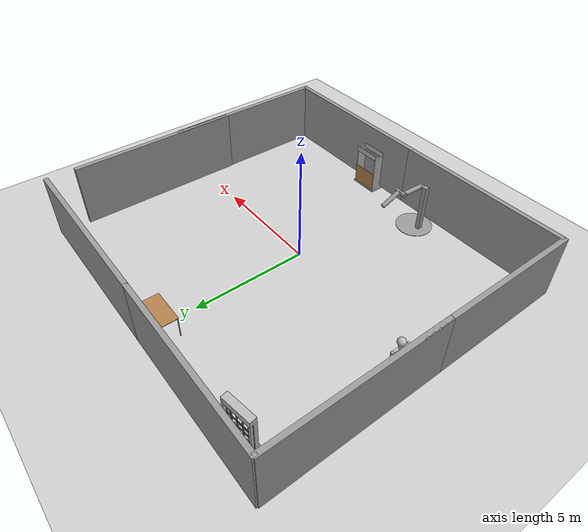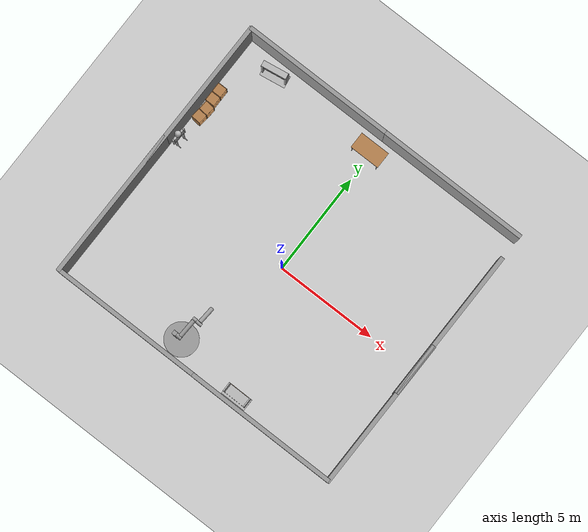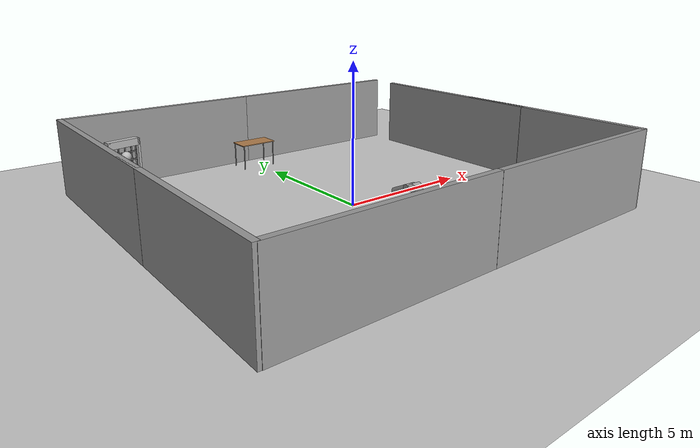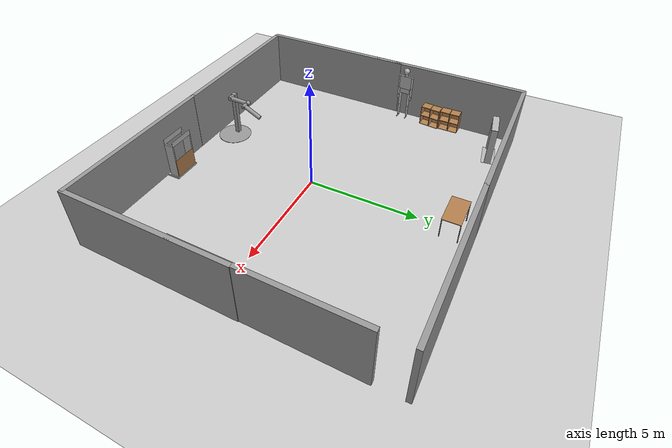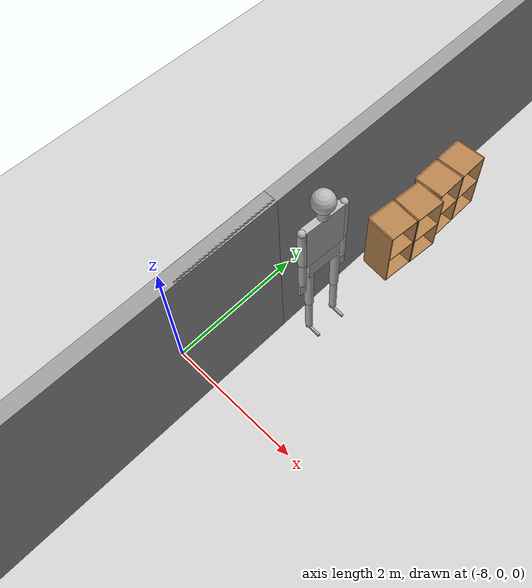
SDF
<sdf version="1.6">
 <world name="default">
  <light name="sun" type="directional">
   <pose>0 0 10 0 -0 0</pose>
   <diffuse>0.8 0.8 0.8 1</diffuse>
   <specular>0.2 0.2 0.2 1</specular>
   <attenuation>
    <range>1000</range>
    <constant>0.9</constant>
    <linear>0.01</linear>
    <quadratic>0.001</quadratic>
   </attenuation>
   <direction>-0.5 0.1 -0.9</direction>
  </light>
  <model name="ground_plane">
   <static>1</static>
   <link name="link">
    <collision name="collision">
     <geometry><plane><normal>0 0 1</normal><size>100 100</size></plane></geometry>
     <surface><friction><ode><mu>100</mu><mu2>50</mu2></ode></friction></surface>
    </collision>
    <visual name="visual">
     <cast_shadows>0</cast_shadows>
     <geometry><plane><normal>0 0 1</normal><size>100 100</size></plane></geometry>
     <material>
      <script><uri>file://media/materials/scripts/gazebo.material</uri><name>Gazebo/Grey</name></script>
     </material>
    </visual>
   </link>
  </model>
  <gravity>0 0 -9.8</gravity>
  <magnetic_field>6e-06 2.3e-05 -4.2e-05</magnetic_field>
  <atmosphere type="adiabatic"/>
  <physics name="default_physics" default="0" type="ode">
   <max_step_size>0.001</max_step_size>
   <real_time_factor>1</real_time_factor>
   <real_time_update_rate>1000</real_time_update_rate>
  </physics>
  <scene><ambient>0.4 0.4 0.4 1</ambient><background>0.7 0.7 0.7 1</background><shadows>1</shadows></scene>
  <audio><device>default</device></audio>
  <spherical_coordinates>
   <surface_model>EARTH_WGS84</surface_model>
   <latitude_deg>0</latitude_deg>
   <longitude_deg>0</longitude_deg>
   <elevation>0</elevation>
   <heading_deg>0</heading_deg>
  </spherical_coordinates>
  <model name="table">
   <static>1</static>
   <link name="link">
    <collision name="surface">
     <pose>0 0 1 0 -0 0</pose>
     <geometry><box><size>1.5 0.8 0.03</size></box></geometry>
     <surface><friction><ode><mu>0.6</mu><mu2>0.6</mu2></ode></friction></surface>
    </collision>
    <visual name="visual1">
     <pose>0 0 1 0 -0 0</pose>
     <geometry><box><size>1.5 0.8 0.03</size></box></geometry>
     <material>
      <script><uri>file://media/materials/scripts/gazebo.material</uri><name>Gazebo/Wood</name></script>
     </material>
    </visual>
    <collision name="front_left_leg">
     <pose>0.68 0.38 0.5 0 -0 0</pose>
     <geometry><cylinder><radius>0.02</radius><length>1</length></cylinder></geometry>
    </collision>
    <visual name="front_left_leg">
     <pose>0.68 0.38 0.5 0 -0 0</pose>
     <geometry><cylinder><radius>0.02</radius><length>1</length></cylinder></geometry>
     <material>
      <script><uri>file://media/materials/scripts/gazebo.material</uri><name>Gazebo/Grey</name></script>
     </material>
    </visual>
    <collision name="front_right_leg">
     <pose>0.68 -0.38 0.5 0 -0 0</pose>
     <geometry><cylinder><radius>0.02</radius><length>1</length></cylinder></geometry>
    </collision>
    <visual name="front_right_leg">
     <pose>0.68 -0.38 0.5 0 -0 0</pose>
     <geometry><cylinder><radius>0.02</radius><length>1</length></cylinder></geometry>
     <material>
      <script><uri>file://media/materials/scripts/gazebo.material</uri><name>Gazebo/Grey</name></script>
     </material>
    </visual>
    <collision name="back_right_leg">
     <pose>-0.68 -0.38 0.5 0 -0 0</pose>
     <geometry><cylinder><radius>0.02</radius><length>1</length></cylinder></geometry>
    </collision>
    <visual name="back_right_leg">
     <pose>-0.68 -0.38 0.5 0 -0 0</pose>
     <geometry><cylinder><radius>0.02</radius><length>1</length></cylinder></geometry>
     <material>
      <script><uri>file://media/materials/scripts/gazebo.material</uri><name>Gazebo/Grey</name></script>
     </material>
    </visual>
    <collision name="back_left_leg">
     <pose>-0.68 0.38 0.5 0 -0 0</pose>
     <geometry><cylinder><radius>0.02</radius><length>1</length></cylinder></geometry>
    </collision>
    <visual name="back_left_leg">
     <pose>-0.68 0.38 0.5 0 -0 0</pose>
     <geometry><cylinder><radius>0.02</radius><length>1</length></cylinder></geometry>
     <material>
      <script><uri>file://media/materials/scripts/gazebo.material</uri><name>Gazebo/Grey</name></script>
     </material>
    </visual>
   </link>
   <pose>-0.108598 6.44893 0 0 -0 0</pose>
  </model>
  <model name="grey_wall">
   <static>1</static>
   <link name="link">
    <pose>0 0 1.4 0 -0 0</pose>
    <collision name="collision"><geometry><box><size>7.5 0.2 2.8</size></box></geometry></collision>
    <visual name="visual">
     <cast_shadows>0</cast_shadows>
     <geometry><box><size>7.5 0.2 2.8</size></box></geometry>
     <material>
      <script>
       <uri>model://grey_wall/materials/scripts</uri>
       <uri>model://grey_wall/materials/textures</uri>
       <name>vrc/grey_wall</name>
      </script>
     </material>
    </visual>
   </link>
   <pose>-3.70916 7.30526 0 0 -0 0</pose>
  </model>
  <model name="grey_wall_clone">
   <static>1</static>
   <link name="link">
    <pose>0 0 1.4 0 -0 0</pose>
    <collision name="collision"><geometry><box><size>7.5 0.2 2.8</size></box></geometry></collision>
    <visual name="visual">
     <cast_shadows>0</cast_shadows>
     <geometry><box><size>7.5 0.2 2.8</size></box></geometry>
     <material>
      <script>
       <uri>model://grey_wall/materials/scripts</uri>
       <uri>model://grey_wall/materials/textures</uri>
       <name>vrc/grey_wall</name>
      </script>
     </material>
    </visual>
   </link>
   <pose>3.72276 7.30577 0 0 -0 0</pose>
  </model>
  <model name="grey_wall_clone_0">
   <static>1</static>
   <link name="link">
    <pose>0 0 1.4 0 -0 0</pose>
    <collision name="collision"><geometry><box><size>7.5 0.2 2.8</size></box></geometry></collision>
    <visual name="visual">
     <cast_shadows>0</cast_shadows>
     <geometry><box><size>7.5 0.2 2.8</size></box></geometry>
     <material>
      <script>
       <uri>model://grey_wall/materials/scripts</uri>
       <uri>model://grey_wall/materials/textures</uri>
       <name>vrc/grey_wall</name>
      </script>
     </material>
    </visual>
   </link>
   <pose>-7.42185 3.59842 0 0 0 -1.57526</pose>
  </model>
  <model name="grey_wall_clone_0_clone">
   <static>1</static>
   <link name="link">
    <pose>0 0 1.4 0 -0 0</pose>
    <collision name="collision"><geometry><box><size>7.5 0.2 2.8</size></box></geometry></collision>
    <visual name="visual">
     <cast_shadows>0</cast_shadows>
     <geometry><box><size>7.5 0.2 2.8</size></box></geometry>
     <material>
      <script>
       <uri>model://grey_wall/materials/scripts</uri>
       <uri>model://grey_wall/materials/textures</uri>
       <name>vrc/grey_wall</name>
      </script>
     </material>
    </visual>
   </link>
   <pose>-7.44688 -2.4911 0 0 0 -1.57526</pose>
  </model>
  <model name="grey_wall_clone_1">
   <static>1</static>
   <link name="link">
    <pose>0 0 1.4 0 -0 0</pose>
    <collision name="collision"><geometry><box><size>7.5 0.2 2.8</size></box></geometry></collision>
    <visual name="visual">
     <cast_shadows>0</cast_shadows>
     <geometry><box><size>7.5 0.2 2.8</size></box></geometry>
     <material>
      <script>
       <uri>model://grey_wall/materials/scripts</uri>
       <uri>model://grey_wall/materials/textures</uri>
       <name>vrc/grey_wall</name>
      </script>
     </material>
    </visual>
   </link>
   <pose>-3.69963 -6.15513 0 0 -0 0</pose>
  </model>
  <model name="grey_wall_clone_clone">
   <static>1</static>
   <link name="link">
    <pose>0 0 1.4 0 -0 0</pose>
    <collision name="collision"><geometry><box><size>7.5 0.2 2.8</size></box></geometry></collision>
    <visual name="visual">
     <cast_shadows>0</cast_shadows>
     <geometry><box><size>7.5 0.2 2.8</size></box></geometry>
     <material>
      <script>
       <uri>model://grey_wall/materials/scripts</uri>
       <uri>model://grey_wall/materials/textures</uri>
       <name>vrc/grey_wall</name>
      </script>
     </material>
    </visual>
   </link>
   <pose>3.65879 -6.15994 0 0 -0 0</pose>
  </model>
  <model name="grey_wall_clone_0_clone_clone">
   <static>1</static>
   <link name="link">
    <pose>0 0 1.4 0 -0 0</pose>
    <collision name="collision"><geometry><box><size>7.5 0.2 2.8</size></box></geometry></collision>
    <visual name="visual">
     <cast_shadows>0</cast_shadows>
     <geometry><box><size>7.5 0.2 2.8</size></box></geometry>
     <material>
      <script>
       <uri>model://grey_wall/materials/scripts</uri>
       <uri>model://grey_wall/materials/textures</uri>
       <name>vrc/grey_wall</name>
      </script>
     </material>
    </visual>
   </link>
   <pose>7.39341 -2.49757 0 0 0 -1.57526</pose>
  </model>
  <model name="grey_wall_clone_0_clone_clone_clone">
   <static>1</static>
   <link name="link">
    <pose>0 0 1.4 0 -0 0</pose>
    <collision name="collision"><geometry><box><size>7.5 0.2 2.8</size></box></geometry></collision>
    <visual name="visual">
     <cast_shadows>0</cast_shadows>
     <geometry><box><size>7.5 0.2 2.8</size></box></geometry>
     <material>
      <script>
       <uri>model://grey_wall/materials/scripts</uri>
       <uri>model://grey_wall/materials/textures</uri>
       <name>vrc/grey_wall</name>
      </script>
     </material>
    </visual>
   </link>
   <pose>7.38705 2.36769 0 0 0 -1.57526</pose>
  </model>
  <model name="double_pendulum_with_base">
   <link name="base">
    <inertial>
     <mass>100</mass>
     <inertia><ixx>1</ixx><ixy>0</ixy><ixz>0</ixz><iyy>1</iyy><iyz>0</iyz><izz>1</izz></inertia>
    </inertial>
    <visual name="vis_plate_on_ground">
     <pose>0 0 0.01 0 -0 0</pose>
     <geometry><cylinder><radius>0.8</radius><length>0.02</length></cylinder></geometry>
     <material>
      <script><uri>file://media/materials/scripts/gazebo.material</uri><name>Gazebo/Grey</name></script>
     </material>
    </visual>
    <visual name="vis_pole">
     <pose>-0.275 0 1.1 0 -0 0</pose>
     <geometry><box><size>0.2 0.2 2.2</size></box></geometry>
     <material>
      <script><uri>file://media/materials/scripts/gazebo.material</uri><name>Gazebo/Grey</name></script>
     </material>
    </visual>
    <collision name="col_plate_on_ground">
     <pose>0 0 0.01 0 -0 0</pose>
     <geometry><cylinder><radius>0.8</radius><length>0.02</length></cylinder></geometry>
    </collision>
    <collision name="col_pole">
     <pose>-0.275 0 1.1 0 -0 0</pose>
     <geometry><box><size>0.2 0.2 2.2</size></box></geometry>
    </collision>
   </link>
   <link name="upper_link">
    <pose>0 0 2.1 -1.5708 0 0</pose>
    <inertial>
     <pose>0 0 0.5 0 -0 0</pose>
     <inertia><ixx>1</ixx><ixy>0</ixy><ixz>0</ixz><iyy>1</iyy><iyz>0</iyz><izz>1</izz></inertia>
     <mass>1</mass>
    </inertial>
    <visual name="vis_upper_joint">
     <pose>-0.05 0 0 3.14159 1.57079 3.14159</pose>
     <geometry><cylinder><radius>0.1</radius><length>0.3</length></cylinder></geometry>
     <material>
      <script><uri>file://media/materials/scripts/gazebo.material</uri><name>Gazebo/Grey</name></script>
     </material>
    </visual>
    <visual name="vis_lower_joint">
     <pose>0 0 1 3.14159 1.57079 3.14159</pose>
     <geometry><cylinder><radius>0.1</radius><length>0.2</length></cylinder></geometry>
     <material>
      <script><uri>file://media/materials/scripts/gazebo.material</uri><name>Gazebo/Grey</name></script>
     </material>
    </visual>
    <visual name="vis_cylinder">
     <pose>0 0 0.5 0 -0 0</pose>
     <geometry><cylinder><radius>0.1</radius><length>0.9</length></cylinder></geometry>
     <material>
      <script><uri>file://media/materials/scripts/gazebo.material</uri><name>Gazebo/Grey</name></script>
     </material>
    </visual>
    <collision name="col_upper_joint">
     <pose>-0.05 0 0 3.14159 1.57079 3.14159</pose>
     <geometry><cylinder><radius>0.1</radius><length>0.3</length></cylinder></geometry>
    </collision>
    <collision name="col_lower_joint">
     <pose>0 0 1 3.14159 1.57079 3.14159</pose>
     <geometry><cylinder><radius>0.1</radius><length>0.2</length></cylinder></geometry>
    </collision>
    <collision name="col_cylinder">
     <pose>0 0 0.5 0 -0 0</pose>
     <geometry><cylinder><radius>0.1</radius><length>0.9</length></cylinder></geometry>
    </collision>
   </link>
   <link name="lower_link">
    <pose>0.25 1 2.1 -2 0 0</pose>
    <inertial>
     <pose>0 0 0.5 0 -0 0</pose>
     <inertia><ixx>1</ixx><ixy>0</ixy><ixz>0</ixz><iyy>1</iyy><iyz>0</iyz><izz>1</izz></inertia>
     <mass>1</mass>
    </inertial>
    <visual name="vis_lower_joint">
     <pose>0 0 0 3.14159 1.57079 3.14159</pose>
     <geometry><cylinder><radius>0.08</radius><length>0.3</length></cylinder></geometry>
     <material>
      <script><uri>file://media/materials/scripts/gazebo.material</uri><name>Gazebo/Grey</name></script>
     </material>
    </visual>
    <visual name="vis_cylinder">
     <pose>0 0 0.5 0 -0 0</pose>
     <geometry><cylinder><radius>0.1</radius><length>0.9</length></cylinder></geometry>
     <material>
      <script><uri>file://media/materials/scripts/gazebo.material</uri><name>Gazebo/Grey</name></script>
     </material>
    </visual>
    <collision name="col_lower_joint">
     <pose>0 0 0 3.14159 1.57079 3.14159</pose>
     <geometry><cylinder><radius>0.08</radius><length>0.3</length></cylinder></geometry>
    </collision>
    <collision name="col_cylinder">
     <pose>0 0 0.5 0 -0 0</pose>
     <geometry><cylinder><radius>0.1</radius><length>0.9</length></cylinder></geometry>
    </collision>
   </link>
   <joint name="upper_joint" type="revolute">
    <parent>base</parent>
    <child>upper_link</child>
    <axis>
     <xyz>1 0 0</xyz>
     <use_parent_model_frame>0</use_parent_model_frame>
     <limit><lower>-1e+16</lower><upper>1e+16</upper></limit>
     <dynamics><spring_reference>0</spring_reference><spring_stiffness>0</spring_stiffness></dynamics>
    </axis>
   </joint>
   <joint name="lower_joint" type="revolute">
    <parent>upper_link</parent>
    <child>lower_link</child>
    <axis>
     <xyz>1 0 0</xyz>
     <use_parent_model_frame>0</use_parent_model_frame>
     <limit><lower>-1e+16</lower><upper>1e+16</upper></limit>
     <dynamics><spring_reference>0</spring_reference><spring_stiffness>0</spring_stiffness></dynamics>
    </axis>
   </joint>
   <pose>-1.56046 -5.23158 0 0 0 -0.040894</pose>
  </model>
  <model name="ragdoll">
   <pose>-7.05606 1.69248 1.39993 -5.4e-05 -0.009344 -0.056737</pose>
   <link name="hip">
    <inertial>
     <inertia><ixx>0.1</ixx><ixy>0</ixy><ixz>0</ixz><iyy>0.1</iyy><iyz>0</iyz><izz>0.1</izz></inertia>
     <mass>10</mass>
    </inertial>
    <collision name="hip_geom">
     <pose>0 0 0.125 0 -0 0</pose>
     <geometry><box><size>0.1 0.5 0.25</size></box></geometry>
     <surface>
      <friction><ode><mu>-1</mu><mu2>-1</mu2><fdir1>0 0 0</fdir1><slip1>0</slip1><slip2>0</slip2></ode></friction>
      <bounce><restitution_coefficient>0</restitution_coefficient><threshold>100000</threshold></bounce>
      <contact>
       <ode>
        <soft_cfm>0</soft_cfm>
        <soft_erp>0.2</soft_erp>
        <kp>1e+12</kp>
        <kd>1</kd>
        <max_vel>0</max_vel>
        <min_depth>0.001</min_depth>
       </ode>
      </contact>
     </surface>
    </collision>
    <visual name="hip_geom_visual">
     <pose>0 0 0.125 0 -0 0</pose>
     <geometry><box><size>0.1 0.5 0.25</size></box></geometry>
    </visual>
    <gravity>0</gravity>
   </link>
   <link name="l_thigh_pan">
    <pose>0 0.22 0 0 -0 0</pose>
    <inertial>
     <inertia><ixx>0.01</ixx><ixy>0</ixy><ixz>0</ixz><iyy>0.01</iyy><iyz>0</iyz><izz>0.01</izz></inertia>
     <mass>1</mass>
    </inertial>
    <collision name="l_thigh_pan_geom">
     <pose>0 0 -0.03 0 -0 0</pose>
     <geometry><sphere><radius>0.06</radius></sphere></geometry>
     <surface>
      <friction><ode><mu>-1</mu><mu2>-1</mu2><fdir1>0 0 0</fdir1><slip1>0</slip1><slip2>0</slip2></ode></friction>
      <bounce><restitution_coefficient>0</restitution_coefficient><threshold>100000</threshold></bounce>
      <contact>
       <ode>
        <soft_cfm>0</soft_cfm>
        <soft_erp>0.2</soft_erp>
        <kp>1e+12</kp>
        <kd>1</kd>
        <max_vel>0</max_vel>
        <min_depth>0.001</min_depth>
       </ode>
      </contact>
     </surface>
    </collision>
    <visual name="l_thigh_pan_geom_visual">
     <pose>0 0 -0.03 0 -0 0</pose>
     <geometry><sphere><radius>0.06</radius></sphere></geometry>
    </visual>
    <gravity>0</gravity>
   </link>
   <link name="l_thigh_lift">
    <pose>0 0.22 0 0 -0 0</pose>
    <inertial>
     <inertia><ixx>0.05</ixx><ixy>0</ixy><ixz>0</ixz><iyy>0.05</iyy><iyz>0</iyz><izz>0.05</izz></inertia>
     <mass>5</mass>
    </inertial>
    <collision name="l_thigh_lift_geom">
     <pose>0 0 -0.35 0 -0 0</pose>
     <geometry><cylinder><radius>0.06</radius><length>0.7</length></cylinder></geometry>
     <surface>
      <friction><ode><mu>-1</mu><mu2>-1</mu2><fdir1>0 0 0</fdir1><slip1>0</slip1><slip2>0</slip2></ode></friction>
      <bounce><restitution_coefficient>0</restitution_coefficient><threshold>100000</threshold></bounce>
      <contact>
       <ode>
        <soft_cfm>0</soft_cfm>
        <soft_erp>0.2</soft_erp>
        <kp>1e+12</kp>
        <kd>1</kd>
        <max_vel>0</max_vel>
        <min_depth>0.001</min_depth>
       </ode>
      </contact>
     </surface>
    </collision>
    <visual name="l_thigh_lift_geom_visual">
     <pose>0 0 -0.35 0 -0 0</pose>
     <geometry><cylinder><radius>0.06</radius><length>0.7</length></cylinder></geometry>
    </visual>
    <gravity>0</gravity>
   </link>
   <link name="l_calf">
    <pose>0 0.22 -0.7 0 -0 0</pose>
    <inertial>
     <inertia><ixx>0.02</ixx><ixy>0</ixy><ixz>0</ixz><iyy>0.02</iyy><iyz>0</iyz><izz>0.02</izz></inertia>
     <mass>2</mass>
    </inertial>
    <collision name="l_calf_geom">
     <pose>0 0 -0.3 0 -0 0</pose>
     <geometry><cylinder><radius>0.05</radius><length>0.6</length></cylinder></geometry>
     <surface>
      <friction><ode><mu>-1</mu><mu2>-1</mu2><fdir1>0 0 0</fdir1><slip1>0</slip1><slip2>0</slip2></ode></friction>
      <bounce><restitution_coefficient>0</restitution_coefficient><threshold>100000</threshold></bounce>
      <contact>
       <ode>
        <soft_cfm>0</soft_cfm>
        <soft_erp>0.2</soft_erp>
        <kp>1e+12</kp>
        <kd>1</kd>
        <max_vel>0</max_vel>
        <min_depth>0.001</min_depth>
       </ode>
      </contact>
     </surface>
    </collision>
    <visual name="l_calf_geom_visual">
     <pose>0 0 -0.3 0 -0 0</pose>
     <geometry><cylinder><radius>0.05</radius><length>0.6</length></cylinder></geometry>
    </visual>
    <gravity>0</gravity>
   </link>
   <link name="l_ankle">
    <pose>0 0.22 -1.325 0 -0 0</pose>
    <inertial>
     <inertia><ixx>0.01</ixx><ixy>0</ixy><ixz>0</ixz><iyy>0.01</iyy><iyz>0</iyz><izz>0.01</izz></inertia>
     <mass>1</mass>
    </inertial>
    <collision name="l_ankle_geom">
     <geometry><sphere><radius>0.05</radius></sphere></geometry>
     <surface>
      <friction><ode><mu>-1</mu><mu2>-1</mu2><fdir1>0 0 0</fdir1><slip1>0</slip1><slip2>0</slip2></ode></friction>
      <bounce><restitution_coefficient>0</restitution_coefficient><threshold>100000</threshold></bounce>
      <contact>
       <ode>
        <soft_cfm>0</soft_cfm>
        <soft_erp>0.2</soft_erp>
        <kp>1e+12</kp>
        <kd>1</kd>
        <max_vel>0</max_vel>
        <min_depth>0.001</min_depth>
       </ode>
      </contact>
     </surface>
    </collision>
    <visual name="l_ankle_geom_visual"><geometry><sphere><radius>0.05</radius></sphere></geometry></visual>
    <gravity>0</gravity>
   </link>
   <link name="l_foot">
    <pose>0 0.22 -1.35 0 -0 0</pose>
    <inertial>
     <pose>0.1 0 0 0 -0 0</pose>
     <inertia><ixx>0.01</ixx><ixy>0</ixy><ixz>0</ixz><iyy>0.01</iyy><iyz>0</iyz><izz>0.01</izz></inertia>
     <mass>1</mass>
    </inertial>
    <collision name="l_foot_geom">
     <pose>0.1 0 -0.025 0 -0 0</pose>
     <geometry><box><size>0.2 0.03 0.05</size></box></geometry>
     <surface>
      <friction><ode><mu>-1</mu><mu2>-1</mu2><fdir1>0 0 0</fdir1><slip1>0</slip1><slip2>0</slip2></ode></friction>
      <bounce><restitution_coefficient>0</restitution_coefficient><threshold>100000</threshold></bounce>
      <contact>
       <ode>
        <soft_cfm>0</soft_cfm>
        <soft_erp>0.2</soft_erp>
        <kp>1e+12</kp>
        <kd>1</kd>
        <max_vel>0</max_vel>
        <min_depth>0.001</min_depth>
       </ode>
      </contact>
     </surface>
    </collision>
    <visual name="l_foot_geom_visual">
     <pose>0.1 0 -0.025 0 -0 0</pose>
     <geometry><box><size>0.2 0.03 0.05</size></box></geometry>
    </visual>
   </link>
   <link name="r_thigh_pan">
    <pose>0 -0.22 0 0 -0 0</pose>
    <inertial>
     <inertia><ixx>0.01</ixx><ixy>0</ixy><ixz>0</ixz><iyy>0.01</iyy><iyz>0</iyz><izz>0.01</izz></inertia>
     <mass>1</mass>
    </inertial>
    <collision name="r_thigh_pan_geom">
     <pose>0 0 -0.03 0 -0 0</pose>
     <geometry><sphere><radius>0.06</radius></sphere></geometry>
     <surface>
      <friction><ode><mu>-1</mu><mu2>-1</mu2><fdir1>0 0 0</fdir1><slip1>0</slip1><slip2>0</slip2></ode></friction>
      <bounce><restitution_coefficient>0</restitution_coefficient><threshold>100000</threshold></bounce>
      <contact>
       <ode>
        <soft_cfm>0</soft_cfm>
        <soft_erp>0.2</soft_erp>
        <kp>1e+12</kp>
        <kd>1</kd>
        <max_vel>0</max_vel>
        <min_depth>0.001</min_depth>
       </ode>
      </contact>
     </surface>
    </collision>
    <visual name="r_thigh_pan_geom_visual">
     <pose>0 0 -0.03 0 -0 0</pose>
     <geometry><sphere><radius>0.06</radius></sphere></geometry>
    </visual>
    <gravity>0</gravity>
   </link>
   <link name="r_thigh_lift">
    <pose>0 -0.22 0 0 -0 0</pose>
    <inertial>
     <inertia><ixx>0.05</ixx><ixy>0</ixy><ixz>0</ixz><iyy>0.05</iyy><iyz>0</iyz><izz>0.05</izz></inertia>
     <mass>5</mass>
    </inertial>
    <collision name="r_thigh_lift_geom">
     <pose>0 0 -0.35 0 -0 0</pose>
     <geometry><cylinder><radius>0.06</radius><length>0.7</length></cylinder></geometry>
     <surface>
      <friction><ode><mu>-1</mu><mu2>-1</mu2><fdir1>0 0 0</fdir1><slip1>0</slip1><slip2>0</slip2></ode></friction>
      <bounce><restitution_coefficient>0</restitution_coefficient><threshold>100000</threshold></bounce>
      <contact>
       <ode>
        <soft_cfm>0</soft_cfm>
        <soft_erp>0.2</soft_erp>
        <kp>1e+12</kp>
        <kd>1</kd>
        <max_vel>0</max_vel>
        <min_depth>0.001</min_depth>
       </ode>
      </contact>
     </surface>
    </collision>
    <visual name="r_thigh_lift_geom_visual">
     <pose>0 0 -0.35 0 -0 0</pose>
     <geometry><cylinder><radius>0.06</radius><length>0.7</length></cylinder></geometry>
    </visual>
    <gravity>0</gravity>
   </link>
   <link name="r_calf">
    <pose>0 -0.22 -0.7 0 -0 0</pose>
    <inertial>
     <inertia><ixx>0.02</ixx><ixy>0</ixy><ixz>0</ixz><iyy>0.02</iyy><iyz>0</iyz><izz>0.02</izz></inertia>
     <mass>2</mass>
    </inertial>
    <collision name="r_calf_geom">
     <pose>0 0 -0.3 0 -0 0</pose>
     <geometry><cylinder><radius>0.05</radius><length>0.6</length></cylinder></geometry>
     <surface>
      <friction><ode><mu>-1</mu><mu2>-1</mu2><fdir1>0 0 0</fdir1><slip1>0</slip1><slip2>0</slip2></ode></friction>
      <bounce><restitution_coefficient>0</restitution_coefficient><threshold>100000</threshold></bounce>
      <contact>
       <ode>
        <soft_cfm>0</soft_cfm>
        <soft_erp>0.2</soft_erp>
        <kp>1e+12</kp>
        <kd>1</kd>
        <max_vel>0</max_vel>
        <min_depth>0.001</min_depth>
       </ode>
      </contact>
     </surface>
    </collision>
    <visual name="r_calf_geom_visual">
     <pose>0 0 -0.3 0 -0 0</pose>
     <geometry><cylinder><radius>0.05</radius><length>0.6</length></cylinder></geometry>
    </visual>
    <gravity>0</gravity>
   </link>
   <link name="r_ankle">
    <pose>0 -0.22 -1.325 0 -0 0</pose>
    <inertial>
     <inertia><ixx>0.01</ixx><ixy>0</ixy><ixz>0</ixz><iyy>0.01</iyy><iyz>0</iyz><izz>0.01</izz></inertia>
     <mass>1</mass>
    </inertial>
    <collision name="r_ankle_geom">
     <geometry><sphere><radius>0.05</radius></sphere></geometry>
     <surface>
      <friction><ode><mu>-1</mu><mu2>-1</mu2><fdir1>0 0 0</fdir1><slip1>0</slip1><slip2>0</slip2></ode></friction>
      <bounce><restitution_coefficient>0</restitution_coefficient><threshold>100000</threshold></bounce>
      <contact>
       <ode>
        <soft_cfm>0</soft_cfm>
        <soft_erp>0.2</soft_erp>
        <kp>1e+12</kp>
        <kd>1</kd>
        <max_vel>0</max_vel>
        <min_depth>0.001</min_depth>
       </ode>
      </contact>
     </surface>
    </collision>
    <visual name="r_ankle_geom_visual"><geometry><sphere><radius>0.05</radius></sphere></geometry></visual>
    <gravity>0</gravity>
   </link>
   <link name="r_foot">
    <pose>0 -0.22 -1.35 0 -0 0</pose>
    <inertial>
     <pose>0.1 0 0 0 -0 0</pose>
     <inertia><ixx>0.01</ixx><ixy>0</ixy><ixz>0</ixz><iyy>0.01</iyy><iyz>0</iyz><izz>0.01</izz></inertia>
     <mass>1</mass>
    </inertial>
    <collision name="r_foot_geom">
     <pose>0.1 0 -0.025 0 -0 0</pose>
     <geometry><box><size>0.2 0.03 0.05</size></box></geometry>
     <surface>
      <friction><ode><mu>-1</mu><mu2>-1</mu2><fdir1>0 0 0</fdir1><slip1>0</slip1><slip2>0</slip2></ode></friction>
      <bounce><restitution_coefficient>0</restitution_coefficient><threshold>100000</threshold></bounce>
      <contact>
       <ode>
        <soft_cfm>0</soft_cfm>
        <soft_erp>0.2</soft_erp>
        <kp>1e+12</kp>
        <kd>1</kd>
        <max_vel>0</max_vel>
        <min_depth>0.001</min_depth>
       </ode>
      </contact>
     </surface>
    </collision>
    <visual name="r_foot_geom_visual">
     <pose>0.1 0 -0.025 0 -0 0</pose>
     <geometry><box><size>0.2 0.03 0.05</size></box></geometry>
    </visual>
   </link>
   <link name="torso">
    <pose>0 0 0.25 0 -0 0</pose>
    <inertial>
     <inertia><ixx>0.3</ixx><ixy>0</ixy><ixz>0</ixz><iyy>0.3</iyy><iyz>0</iyz><izz>0.3</izz></inertia>
     <mass>30</mass>
    </inertial>
    <collision name="torso_geom">
     <pose>0 0 0.35 0 -0 0</pose>
     <geometry><box><size>0.1 0.6 0.7</size></box></geometry>
     <surface>
      <friction><ode><mu>-1</mu><mu2>-1</mu2><fdir1>0 0 0</fdir1><slip1>0</slip1><slip2>0</slip2></ode></friction>
      <bounce><restitution_coefficient>0</restitution_coefficient><threshold>100000</threshold></bounce>
      <contact>
       <ode>
        <soft_cfm>0</soft_cfm>
        <soft_erp>0.2</soft_erp>
        <kp>1e+12</kp>
        <kd>1</kd>
        <max_vel>0</max_vel>
        <min_depth>0.001</min_depth>
       </ode>
      </contact>
     </surface>
    </collision>
    <visual name="torso_geom_visual">
     <pose>0 0 0.35 0 -0 0</pose>
     <geometry><box><size>0.1 0.6 0.7</size></box></geometry>
    </visual>
    <gravity>0</gravity>
   </link>
   <link name="l_shoulder">
    <pose>0 0.3275 0.9225 0 -0 0</pose>
    <inertial>
     <inertia><ixx>0.01</ixx><ixy>0</ixy><ixz>0</ixz><iyy>0.01</iyy><iyz>0</iyz><izz>0.01</izz></inertia>
     <mass>1</mass>
    </inertial>
    <collision name="l_shoulder_geom">
     <geometry><sphere><radius>0.055</radius></sphere></geometry>
     <surface>
      <friction><ode><mu>-1</mu><mu2>-1</mu2><fdir1>0 0 0</fdir1><slip1>0</slip1><slip2>0</slip2></ode></friction>
      <bounce><restitution_coefficient>0</restitution_coefficient><threshold>100000</threshold></bounce>
      <contact>
       <ode>
        <soft_cfm>0</soft_cfm>
        <soft_erp>0.2</soft_erp>
        <kp>1e+12</kp>
        <kd>1</kd>
        <max_vel>0</max_vel>
        <min_depth>0.001</min_depth>
       </ode>
      </contact>
     </surface>
    </collision>
    <visual name="l_shoulder_geom_visual"><geometry><sphere><radius>0.055</radius></sphere></geometry></visual>
    <gravity>0</gravity>
   </link>
   <link name="l_upper_arm">
    <pose>0 0.3275 0.9225 0 -0 0</pose>
    <inertial>
     <inertia><ixx>0.02</ixx><ixy>0</ixy><ixz>0</ixz><iyy>0.02</iyy><iyz>0</iyz><izz>0.02</izz></inertia>
     <mass>2</mass>
    </inertial>
    <collision name="l_upper_arm_geom">
     <pose>0 0 -0.3 0 -0 0</pose>
     <geometry><cylinder><radius>0.055</radius><length>0.6</length></cylinder></geometry>
     <surface>
      <friction><ode><mu>-1</mu><mu2>-1</mu2><fdir1>0 0 0</fdir1><slip1>0</slip1><slip2>0</slip2></ode></friction>
      <bounce><restitution_coefficient>0</restitution_coefficient><threshold>100000</threshold></bounce>
      <contact>
       <ode>
        <soft_cfm>0</soft_cfm>
        <soft_erp>0.2</soft_erp>
        <kp>1e+12</kp>
        <kd>1</kd>
        <max_vel>0</max_vel>
        <min_depth>0.001</min_depth>
       </ode>
      </contact>
     </surface>
    </collision>
    <visual name="l_upper_arm_geom_visual">
     <pose>0 0 -0.3 0 -0 0</pose>
     <geometry><cylinder><radius>0.055</radius><length>0.6</length></cylinder></geometry>
    </visual>
    <gravity>0</gravity>
   </link>
   <link name="l_forearm">
    <pose>0 0.3275 0.3225 0 -0 0</pose>
    <inertial>
     <inertia><ixx>0.01</ixx><ixy>0</ixy><ixz>0</ixz><iyy>0.01</iyy><iyz>0</iyz><izz>0.01</izz></inertia>
     <mass>1</mass>
    </inertial>
    <collision name="l_forearm_geom">
     <pose>0 0 -0.225 0 -0 0</pose>
     <geometry><cylinder><radius>0.05</radius><length>0.45</length></cylinder></geometry>
     <surface>
      <friction><ode><mu>-1</mu><mu2>-1</mu2><fdir1>0 0 0</fdir1><slip1>0</slip1><slip2>0</slip2></ode></friction>
      <bounce><restitution_coefficient>0</restitution_coefficient><threshold>100000</threshold></bounce>
      <contact>
       <ode>
        <soft_cfm>0</soft_cfm>
        <soft_erp>0.2</soft_erp>
        <kp>1e+12</kp>
        <kd>1</kd>
        <max_vel>0</max_vel>
        <min_depth>0.001</min_depth>
       </ode>
      </contact>
     </surface>
    </collision>
    <visual name="l_forearm_geom_visual">
     <pose>0 0 -0.225 0 -0 0</pose>
     <geometry><cylinder><radius>0.05</radius><length>0.45</length></cylinder></geometry>
    </visual>
    <gravity>0</gravity>
   </link>
   <link name="l_wrist">
    <pose>0 0.3275 -0.1425 0 -0 0</pose>
    <inertial>
     <inertia><ixx>0.01</ixx><ixy>0</ixy><ixz>0</ixz><iyy>0.01</iyy><iyz>0</iyz><izz>0.01</izz></inertia>
     <mass>1</mass>
    </inertial>
    <collision name="l_wrist_geom">
     <geometry><sphere><radius>0.03</radius></sphere></geometry>
     <surface>
      <friction><ode><mu>-1</mu><mu2>-1</mu2><fdir1>0 0 0</fdir1><slip1>0</slip1><slip2>0</slip2></ode></friction>
      <bounce><restitution_coefficient>0</restitution_coefficient><threshold>100000</threshold></bounce>
      <contact>
       <ode>
        <soft_cfm>0</soft_cfm>
        <soft_erp>0.2</soft_erp>
        <kp>1e+12</kp>
        <kd>1</kd>
        <max_vel>0</max_vel>
        <min_depth>0.001</min_depth>
       </ode>
      </contact>
     </surface>
    </collision>
    <visual name="l_wrist_geom_visual"><geometry><sphere><radius>0.03</radius></sphere></geometry></visual>
    <gravity>0</gravity>
   </link>
   <link name="l_hand">
    <pose>0 0.3275 -0.1575 0 -0 0</pose>
    <inertial>
     <inertia><ixx>0.01</ixx><ixy>0</ixy><ixz>0</ixz><iyy>0.01</iyy><iyz>0</iyz><izz>0.01</izz></inertia>
     <mass>1</mass>
    </inertial>
    <collision name="l_hand_geom">
     <pose>0 0 -0.1 0 -0 0</pose>
     <geometry><box><size>0.03 0.1 0.2</size></box></geometry>
     <surface>
      <friction><ode><mu>-1</mu><mu2>-1</mu2><fdir1>0 0 0</fdir1><slip1>0</slip1><slip2>0</slip2></ode></friction>
      <bounce><restitution_coefficient>0</restitution_coefficient><threshold>100000</threshold></bounce>
      <contact>
       <ode>
        <soft_cfm>0</soft_cfm>
        <soft_erp>0.2</soft_erp>
        <kp>1e+12</kp>
        <kd>1</kd>
        <max_vel>0</max_vel>
        <min_depth>0.001</min_depth>
       </ode>
      </contact>
     </surface>
    </collision>
    <visual name="l_hand_geom_visual">
     <pose>0 0 -0.1 0 -0 0</pose>
     <geometry><box><size>0.03 0.1 0.2</size></box></geometry>
    </visual>
    <gravity>0</gravity>
   </link>
   <link name="neck">
    <pose>0 0 0.95 0 -0 0</pose>
    <inertial>
     <inertia><ixx>0.01</ixx><ixy>0</ixy><ixz>0</ixz><iyy>0.01</iyy><iyz>0</iyz><izz>0.01</izz></inertia>
     <mass>1</mass>
    </inertial>
    <collision name="neck_geom">
     <pose>0 0 0.1 0 -0 0</pose>
     <geometry><cylinder><radius>0.075</radius><length>0.2</length></cylinder></geometry>
     <surface>
      <friction><ode><mu>-1</mu><mu2>-1</mu2><fdir1>0 0 0</fdir1><slip1>0</slip1><slip2>0</slip2></ode></friction>
      <bounce><restitution_coefficient>0</restitution_coefficient><threshold>100000</threshold></bounce>
      <contact>
       <ode>
        <soft_cfm>0</soft_cfm>
        <soft_erp>0.2</soft_erp>
        <kp>1e+12</kp>
        <kd>1</kd>
        <max_vel>0</max_vel>
        <min_depth>0.001</min_depth>
       </ode>
      </contact>
     </surface>
    </collision>
    <visual name="neck_geom_visual">
     <pose>0 0 0.1 0 -0 0</pose>
     <geometry><cylinder><radius>0.075</radius><length>0.2</length></cylinder></geometry>
    </visual>
    <gravity>0</gravity>
   </link>
   <link name="head">
    <pose>0 0 1.225 0 -0 0</pose>
    <inertial>
     <inertia><ixx>0.1</ixx><ixy>0</ixy><ixz>0</ixz><iyy>0.1</iyy><iyz>0</iyz><izz>0.1</izz></inertia>
     <mass>10</mass>
    </inertial>
    <collision name="head_geom">
     <geometry><sphere><radius>0.15</radius></sphere></geometry>
     <surface>
      <friction><ode><mu>-1</mu><mu2>-1</mu2><fdir1>0 0 0</fdir1><slip1>0</slip1><slip2>0</slip2></ode></friction>
      <bounce><restitution_coefficient>0</restitution_coefficient><threshold>100000</threshold></bounce>
      <contact>
       <ode>
        <soft_cfm>0</soft_cfm>
        <soft_erp>0.2</soft_erp>
        <kp>1e+12</kp>
        <kd>1</kd>
        <max_vel>0</max_vel>
        <min_depth>0.001</min_depth>
       </ode>
      </contact>
     </surface>
    </collision>
    <visual name="head_geom_visual"><geometry><sphere><radius>0.15</radius></sphere></geometry></visual>
    <gravity>0</gravity>
   </link>
   <link name="r_shoulder">
    <pose>0 -0.3275 0.9225 0 -0 0</pose>
    <inertial>
     <inertia><ixx>0.01</ixx><ixy>0</ixy><ixz>0</ixz><iyy>0.01</iyy><iyz>0</iyz><izz>0.01</izz></inertia>
     <mass>1</mass>
    </inertial>
    <collision name="r_shoulder_geom">
     <geometry><sphere><radius>0.055</radius></sphere></geometry>
     <surface>
      <friction><ode><mu>-1</mu><mu2>-1</mu2><fdir1>0 0 0</fdir1><slip1>0</slip1><slip2>0</slip2></ode></friction>
      <bounce><restitution_coefficient>0</restitution_coefficient><threshold>100000</threshold></bounce>
      <contact>
       <ode>
        <soft_cfm>0</soft_cfm>
        <soft_erp>0.2</soft_erp>
        <kp>1e+12</kp>
        <kd>1</kd>
        <max_vel>0</max_vel>
        <min_depth>0.001</min_depth>
       </ode>
      </contact>
     </surface>
    </collision>
    <visual name="r_shoulder_geom_visual"><geometry><sphere><radius>0.055</radius></sphere></geometry></visual>
    <gravity>0</gravity>
   </link>
   <link name="r_upper_arm">
    <pose>0 -0.3275 0.9225 0 -0 0</pose>
    <inertial>
     <inertia><ixx>0.02</ixx><ixy>0</ixy><ixz>0</ixz><iyy>0.02</iyy><iyz>0</iyz><izz>0.02</izz></inertia>
     <mass>2</mass>
    </inertial>
    <collision name="r_upper_arm_geom">
     <pose>0 0 -0.3 0 -0 0</pose>
     <geometry><cylinder><radius>0.055</radius><length>0.6</length></cylinder></geometry>
     <surface>
      <friction><ode><mu>-1</mu><mu2>-1</mu2><fdir1>0 0 0</fdir1><slip1>0</slip1><slip2>0</slip2></ode></friction>
      <bounce><restitution_coefficient>0</restitution_coefficient><threshold>100000</threshold></bounce>
      <contact>
       <ode>
        <soft_cfm>0</soft_cfm>
        <soft_erp>0.2</soft_erp>
        <kp>1e+12</kp>
        <kd>1</kd>
        <max_vel>0</max_vel>
        <min_depth>0.001</min_depth>
       </ode>
      </contact>
     </surface>
    </collision>
    <visual name="r_upper_arm_geom_visual">
     <pose>0 0 -0.3 0 -0 0</pose>
     <geometry><cylinder><radius>0.055</radius><length>0.6</length></cylinder></geometry>
    </visual>
    <gravity>0</gravity>
   </link>
   <link name="r_forearm">
    <pose>0 -0.3275 0.3225 0 -0 0</pose>
    <inertial>
     <inertia><ixx>0.01</ixx><ixy>0</ixy><ixz>0</ixz><iyy>0.01</iyy><iyz>0</iyz><izz>0.01</izz></inertia>
     <mass>1</mass>
    </inertial>
    <collision name="r_forearm_geom">
     <pose>0 0 -0.225 0 -0 0</pose>
     <geometry><cylinder><radius>0.05</radius><length>0.45</length></cylinder></geometry>
     <surface>
      <friction><ode><mu>-1</mu><mu2>-1</mu2><fdir1>0 0 0</fdir1><slip1>0</slip1><slip2>0</slip2></ode></friction>
      <bounce><restitution_coefficient>0</restitution_coefficient><threshold>100000</threshold></bounce>
      <contact>
       <ode>
        <soft_cfm>0</soft_cfm>
        <soft_erp>0.2</soft_erp>
        <kp>1e+12</kp>
        <kd>1</kd>
        <max_vel>0</max_vel>
        <min_depth>0.001</min_depth>
       </ode>
      </contact>
     </surface>
    </collision>
    <visual name="r_forearm_geom_visual">
     <pose>0 0 -0.225 0 -0 0</pose>
     <geometry><cylinder><radius>0.05</radius><length>0.45</length></cylinder></geometry>
    </visual>
    <gravity>0</gravity>
   </link>
   <link name="r_wrist">
    <pose>0 -0.3275 -0.1425 0 -0 0</pose>
    <inertial>
     <inertia><ixx>0.01</ixx><ixy>0</ixy><ixz>0</ixz><iyy>0.01</iyy><iyz>0</iyz><izz>0.01</izz></inertia>
     <mass>1</mass>
    </inertial>
    <collision name="r_wrist_geom">
     <geometry><sphere><radius>0.03</radius></sphere></geometry>
     <surface>
      <friction><ode><mu>-1</mu><mu2>-1</mu2><fdir1>0 0 0</fdir1><slip1>0</slip1><slip2>0</slip2></ode></friction>
      <bounce><restitution_coefficient>0</restitution_coefficient><threshold>100000</threshold></bounce>
      <contact>
       <ode>
        <soft_cfm>0</soft_cfm>
        <soft_erp>0.2</soft_erp>
        <kp>1e+12</kp>
        <kd>1</kd>
        <max_vel>0</max_vel>
        <min_depth>0.001</min_depth>
       </ode>
      </contact>
     </surface>
    </collision>
    <visual name="r_wrist_geom_visual"><geometry><sphere><radius>0.03</radius></sphere></geometry></visual>
    <gravity>0</gravity>
   </link>
   <link name="r_hand">
    <pose>0 -0.3275 -0.1575 0 -0 0</pose>
    <inertial>
     <inertia><ixx>0.01</ixx><ixy>0</ixy><ixz>0</ixz><iyy>0.01</iyy><iyz>0</iyz><izz>0.01</izz></inertia>
     <mass>1</mass>
    </inertial>
    <collision name="r_hand_geom">
     <pose>0 0 -0.1 0 -0 0</pose>
     <geometry><box><size>0.03 0.1 0.2</size></box></geometry>
     <surface>
      <friction><ode><mu>-1</mu><mu2>-1</mu2><fdir1>0 0 0</fdir1><slip1>0</slip1><slip2>0</slip2></ode></friction>
      <bounce><restitution_coefficient>0</restitution_coefficient><threshold>100000</threshold></bounce>
      <contact>
       <ode>
        <soft_cfm>0</soft_cfm>
        <soft_erp>0.2</soft_erp>
        <kp>1e+12</kp>
        <kd>1</kd>
        <max_vel>0</max_vel>
        <min_depth>0.001</min_depth>
       </ode>
      </contact>
     </surface>
    </collision>
    <visual name="r_hand_geom_visual">
     <pose>0 0 -0.1 0 -0 0</pose>
     <geometry><box><size>0.03 0.1 0.2</size></box></geometry>
    </visual>
    <gravity>0</gravity>
   </link>
   <joint name="l_thigh_pan_joint" type="revolute">
    <parent>hip</parent>
    <child>l_thigh_pan</child>
    <axis>
     <dynamics>
      <damping>0</damping>
      <friction>0</friction>
      <spring_reference>0</spring_reference>
      <spring_stiffness>0</spring_stiffness>
     </dynamics>
     <limit><lower>-1.5708</lower><upper>1.5708</upper><effort>0</effort><velocity>0</velocity></limit>
     <xyz>0 0 1</xyz>
     <use_parent_model_frame>1</use_parent_model_frame>
    </axis>
   </joint>
   <joint name="l_thigh_lift_joint" type="revolute">
    <parent>l_thigh_pan</parent>
    <child>l_thigh_lift</child>
    <axis>
     <dynamics>
      <damping>0</damping>
      <friction>0</friction>
      <spring_reference>0</spring_reference>
      <spring_stiffness>0</spring_stiffness>
     </dynamics>
     <limit><lower>-1.5708</lower><upper>1.5708</upper><effort>0</effort><velocity>0</velocity></limit>
     <xyz>0 1 0</xyz>
     <use_parent_model_frame>1</use_parent_model_frame>
    </axis>
   </joint>
   <joint name="l_calf_joint" type="revolute">
    <parent>l_thigh_lift</parent>
    <child>l_calf</child>
    <axis>
     <dynamics>
      <damping>0</damping>
      <friction>0</friction>
      <spring_reference>0</spring_reference>
      <spring_stiffness>0</spring_stiffness>
     </dynamics>
     <limit><lower>-1.5708</lower><upper>1.5708</upper><effort>0</effort><velocity>0</velocity></limit>
     <xyz>0 1 0</xyz>
     <use_parent_model_frame>1</use_parent_model_frame>
    </axis>
   </joint>
   <joint name="l_ankle_joint" type="revolute">
    <parent>l_calf</parent>
    <child>l_ankle</child>
    <axis>
     <dynamics>
      <damping>0</damping>
      <friction>0</friction>
      <spring_reference>0</spring_reference>
      <spring_stiffness>0</spring_stiffness>
     </dynamics>
     <limit><lower>-1.5708</lower><upper>1.5708</upper><effort>0</effort><velocity>0</velocity></limit>
     <xyz>0 1 0</xyz>
     <use_parent_model_frame>1</use_parent_model_frame>
    </axis>
   </joint>
   <joint name="l_foot_joint" type="revolute">
    <parent>l_ankle</parent>
    <child>l_foot</child>
    <axis>
     <dynamics>
      <damping>0</damping>
      <friction>0</friction>
      <spring_reference>0</spring_reference>
      <spring_stiffness>0</spring_stiffness>
     </dynamics>
     <limit><lower>-1.5708</lower><upper>1.5708</upper><effort>0</effort><velocity>0</velocity></limit>
     <xyz>1 0 0</xyz>
     <use_parent_model_frame>1</use_parent_model_frame>
    </axis>
   </joint>
   <joint name="r_thigh_pan_joint" type="revolute">
    <parent>hip</parent>
    <child>r_thigh_pan</child>
    <axis>
     <dynamics>
      <damping>0</damping>
      <friction>0</friction>
      <spring_reference>0</spring_reference>
      <spring_stiffness>0</spring_stiffness>
     </dynamics>
     <limit><lower>-1.5708</lower><upper>1.5708</upper><effort>0</effort><velocity>0</velocity></limit>
     <xyz>0 0 1</xyz>
     <use_parent_model_frame>1</use_parent_model_frame>
    </axis>
   </joint>
   <joint name="r_thigh_lift_joint" type="revolute">
    <parent>r_thigh_pan</parent>
    <child>r_thigh_lift</child>
    <axis>
     <dynamics>
      <damping>0</damping>
      <friction>0</friction>
      <spring_reference>0</spring_reference>
      <spring_stiffness>0</spring_stiffness>
     </dynamics>
     <limit><lower>-1.5708</lower><upper>1.5708</upper><effort>0</effort><velocity>0</velocity></limit>
     <xyz>0 1 0</xyz>
     <use_parent_model_frame>1</use_parent_model_frame>
    </axis>
   </joint>
   <joint name="r_calf_joint" type="revolute">
    <parent>r_thigh_lift</parent>
    <child>r_calf</child>
    <axis>
     <dynamics>
      <damping>0</damping>
      <friction>0</friction>
      <spring_reference>0</spring_reference>
      <spring_stiffness>0</spring_stiffness>
     </dynamics>
     <limit><lower>-1.5708</lower><upper>1.5708</upper><effort>0</effort><velocity>0</velocity></limit>
     <xyz>0 1 0</xyz>
     <use_parent_model_frame>1</use_parent_model_frame>
    </axis>
   </joint>
   <joint name="r_ankle_joint" type="revolute">
    <parent>r_calf</parent>
    <child>r_ankle</child>
    <axis>
     <dynamics>
      <damping>0</damping>
      <friction>0</friction>
      <spring_reference>0</spring_reference>
      <spring_stiffness>0</spring_stiffness>
     </dynamics>
     <limit><lower>-1.5708</lower><upper>1.5708</upper><effort>0</effort><velocity>0</velocity></limit>
     <xyz>0 1 0</xyz>
     <use_parent_model_frame>1</use_parent_model_frame>
    </axis>
   </joint>
   <joint name="r_foot_joint" type="revolute">
    <parent>r_ankle</parent>
    <child>r_foot</child>
    <axis>
     <dynamics>
      <damping>0</damping>
      <friction>0</friction>
      <spring_reference>0</spring_reference>
      <spring_stiffness>0</spring_stiffness>
     </dynamics>
     <limit><lower>-1.5708</lower><upper>1.5708</upper><effort>0</effort><velocity>0</velocity></limit>
     <xyz>1 0 0</xyz>
     <use_parent_model_frame>1</use_parent_model_frame>
    </axis>
   </joint>
   <joint name="torso_joint" type="revolute">
    <parent>hip</parent>
    <child>torso</child>
    <axis>
     <dynamics>
      <damping>0</damping>
      <friction>0</friction>
      <spring_reference>0</spring_reference>
      <spring_stiffness>0</spring_stiffness>
     </dynamics>
     <limit><lower>-1.5708</lower><upper>1.5708</upper><effort>0</effort><velocity>0</velocity></limit>
     <xyz>0 1 0</xyz>
     <use_parent_model_frame>1</use_parent_model_frame>
    </axis>
   </joint>
   <joint name="l_shoulder_joint" type="revolute">
    <parent>torso</parent>
    <child>l_shoulder</child>
    <axis>
     <dynamics>
      <damping>0</damping>
      <friction>0</friction>
      <spring_reference>0</spring_reference>
      <spring_stiffness>0</spring_stiffness>
     </dynamics>
     <limit><lower>-1.5708</lower><upper>1.5708</upper><effort>0</effort><velocity>0</velocity></limit>
     <xyz>1 0 0</xyz>
     <use_parent_model_frame>1</use_parent_model_frame>
    </axis>
   </joint>
   <joint name="l_upper_arm_joint" type="revolute">
    <parent>l_shoulder</parent>
    <child>l_upper_arm</child>
    <axis>
     <dynamics>
      <damping>0</damping>
      <friction>0</friction>
      <spring_reference>0</spring_reference>
      <spring_stiffness>0</spring_stiffness>
     </dynamics>
     <limit><lower>-1.5708</lower><upper>1.5708</upper><effort>0</effort><velocity>0</velocity></limit>
     <xyz>0 1 0</xyz>
     <use_parent_model_frame>1</use_parent_model_frame>
    </axis>
   </joint>
   <joint name="l_forearm_joint" type="revolute">
    <parent>l_upper_arm</parent>
    <child>l_forearm</child>
    <axis>
     <dynamics>
      <damping>0</damping>
      <friction>0</friction>
      <spring_reference>0</spring_reference>
      <spring_stiffness>0</spring_stiffness>
     </dynamics>
     <limit><lower>-1.5708</lower><upper>1.5708</upper><effort>0</effort><velocity>0</velocity></limit>
     <xyz>0 1 0</xyz>
     <use_parent_model_frame>1</use_parent_model_frame>
    </axis>
   </joint>
   <joint name="l_wrist_joint" type="revolute">
    <parent>l_forearm</parent>
    <child>l_wrist</child>
    <axis>
     <dynamics>
      <damping>0</damping>
      <friction>0</friction>
      <spring_reference>0</spring_reference>
      <spring_stiffness>0</spring_stiffness>
     </dynamics>
     <limit><lower>-1.5708</lower><upper>1.5708</upper><effort>0</effort><velocity>0</velocity></limit>
     <xyz>0 1 0</xyz>
     <use_parent_model_frame>1</use_parent_model_frame>
    </axis>
   </joint>
   <joint name="l_hand_joint" type="revolute">
    <parent>l_wrist</parent>
    <child>l_hand</child>
    <axis>
     <dynamics>
      <damping>0</damping>
      <friction>0</friction>
      <spring_reference>0</spring_reference>
      <spring_stiffness>0</spring_stiffness>
     </dynamics>
     <limit><lower>-1.5708</lower><upper>1.5708</upper><effort>0</effort><velocity>0</velocity></limit>
     <xyz>0 1 0</xyz>
     <use_parent_model_frame>1</use_parent_model_frame>
    </axis>
   </joint>
   <joint name="neck_joint" type="revolute">
    <parent>torso</parent>
    <child>neck</child>
    <axis>
     <dynamics>
      <damping>0</damping>
      <friction>0</friction>
      <spring_reference>0</spring_reference>
      <spring_stiffness>0</spring_stiffness>
     </dynamics>
     <limit><lower>-1.5708</lower><upper>1.5708</upper><effort>0</effort><velocity>0</velocity></limit>
     <xyz>0 0 1</xyz>
     <use_parent_model_frame>1</use_parent_model_frame>
    </axis>
   </joint>
   <joint name="head_joint" type="revolute">
    <parent>neck</parent>
    <child>head</child>
    <axis>
     <dynamics>
      <damping>0</damping>
      <friction>0</friction>
      <spring_reference>0</spring_reference>
      <spring_stiffness>0</spring_stiffness>
     </dynamics>
     <limit><lower>-1.5708</lower><upper>1.5708</upper><effort>0</effort><velocity>0</velocity></limit>
     <xyz>0 1 0</xyz>
     <use_parent_model_frame>1</use_parent_model_frame>
    </axis>
   </joint>
   <joint name="r_shoulder_joint" type="revolute">
    <parent>torso</parent>
    <child>r_shoulder</child>
    <axis>
     <dynamics>
      <damping>0</damping>
      <friction>0</friction>
      <spring_reference>0</spring_reference>
      <spring_stiffness>0</spring_stiffness>
     </dynamics>
     <limit><lower>-1.5708</lower><upper>1.5708</upper><effort>0</effort><velocity>0</velocity></limit>
     <xyz>1 0 0</xyz>
     <use_parent_model_frame>1</use_parent_model_frame>
    </axis>
   </joint>
   <joint name="r_upper_arm_joint" type="revolute">
    <parent>r_shoulder</parent>
    <child>r_upper_arm</child>
    <axis>
     <dynamics>
      <damping>0</damping>
      <friction>0</friction>
      <spring_reference>0</spring_reference>
      <spring_stiffness>0</spring_stiffness>
     </dynamics>
     <limit><lower>-1.5708</lower><upper>1.5708</upper><effort>0</effort><velocity>0</velocity></limit>
     <xyz>0 1 0</xyz>
     <use_parent_model_frame>1</use_parent_model_frame>
    </axis>
   </joint>
   <joint name="r_forearm_joint" type="revolute">
    <parent>r_upper_arm</parent>
    <child>r_forearm</child>
    <axis>
     <dynamics>
      <damping>0</damping>
      <friction>0</friction>
      <spring_reference>0</spring_reference>
      <spring_stiffness>0</spring_stiffness>
     </dynamics>
     <limit><lower>-1.5708</lower><upper>1.5708</upper><effort>0</effort><velocity>0</velocity></limit>
     <xyz>0 1 0</xyz>
     <use_parent_model_frame>1</use_parent_model_frame>
    </axis>
   </joint>
   <joint name="r_wrist_joint" type="revolute">
    <parent>r_forearm</parent>
    <child>r_wrist</child>
    <axis>
     <dynamics>
      <damping>0</damping>
      <friction>0</friction>
      <spring_reference>0</spring_reference>
      <spring_stiffness>0</spring_stiffness>
     </dynamics>
     <limit><lower>-1.5708</lower><upper>1.5708</upper><effort>0</effort><velocity>0</velocity></limit>
     <xyz>0 1 0</xyz>
     <use_parent_model_frame>1</use_parent_model_frame>
    </axis>
   </joint>
   <joint name="r_hand_joint" type="revolute">
    <parent>r_wrist</parent>
    <child>r_hand</child>
    <axis>
     <dynamics>
      <damping>0</damping>
      <friction>0</friction>
      <spring_reference>0</spring_reference>
      <spring_stiffness>0</spring_stiffness>
     </dynamics>
     <limit><lower>-1.5708</lower><upper>1.5708</upper><effort>0</effort><velocity>0</velocity></limit>
     <xyz>0 1 0</xyz>
     <use_parent_model_frame>1</use_parent_model_frame>
    </axis>
   </joint>
   <static>0</static>
  </model>
  <model name="cabinet">
   <static>1</static>
   <link name="cabinet_bottom_plate">
    <inertial>
     <pose>0 0 -1 0 -0 0</pose>
     <inertia><ixx>2.05</ixx><ixy>0</ixy><ixz>0</ixz><iyy>2.05</iyy><iyz>0</iyz><izz>2.05</izz></inertia>
     <mass>25</mass>
    </inertial>
    <collision name="cabinet_bottom_plate_geom">
     <pose>0 0 0.01 0 -0 0</pose>
     <geometry><box><size>0.45 0.45 0.02</size></box></geometry>
    </collision>
    <visual name="cabinet_bottom_plate_geom_visual">
     <pose>0 0 0.01 0 -0 0</pose>
     <geometry><box><size>0.45 0.45 0.02</size></box></geometry>
     <material>
      <script><uri>file://media/materials/scripts/gazebo.material</uri><name>Gazebo/Wood</name></script>
     </material>
    </visual>
    <collision name="cabinet_bottom_plate_geom_cabinet_back_plate">
     <pose>0.235 0 0.51 0 -0 0</pose>
     <geometry><box><size>0.02 0.45 1.02</size></box></geometry>
    </collision>
    <visual name="cabinet_bottom_plate_geom_cabinet_back_plate_visual">
     <pose>0.235 0 0.51 0 -0 0</pose>
     <geometry><box><size>0.02 0.45 1.02</size></box></geometry>
     <material>
      <script><uri>file://media/materials/scripts/gazebo.material</uri><name>Gazebo/Wood</name></script>
     </material>
    </visual>
    <collision name="cabinet_bottom_plate_geom_cabinet_left_plate">
     <pose>0 0.235 0.51 0 -0 0</pose>
     <geometry><box><size>0.45 0.02 1.02</size></box></geometry>
    </collision>
    <visual name="cabinet_bottom_plate_geom_cabinet_left_plate_visual">
     <pose>0 0.235 0.51 0 -0 0</pose>
     <geometry><box><size>0.45 0.02 1.02</size></box></geometry>
     <material>
      <script><uri>file://media/materials/scripts/gazebo.material</uri><name>Gazebo/Wood</name></script>
     </material>
    </visual>
    <collision name="cabinet_bottom_plate_geom_cabinet_middle_plate">
     <pose>0 0 0.51 0 -0 0</pose>
     <geometry><box><size>0.45 0.45 0.02</size></box></geometry>
    </collision>
    <visual name="cabinet_bottom_plate_geom_cabinet_middle_plate_visual">
     <pose>0 0 0.51 0 -0 0</pose>
     <geometry><box><size>0.45 0.45 0.02</size></box></geometry>
     <material>
      <script><uri>file://media/materials/scripts/gazebo.material</uri><name>Gazebo/Wood</name></script>
     </material>
    </visual>
    <collision name="cabinet_bottom_plate_geom_cabinet_right_plate">
     <pose>0 -0.235 0.51 0 -0 0</pose>
     <geometry><box><size>0.45 0.02 1.02</size></box></geometry>
    </collision>
    <visual name="cabinet_bottom_plate_geom_cabinet_right_plate_visual">
     <pose>0 -0.235 0.51 0 -0 0</pose>
     <geometry><box><size>0.45 0.02 1.02</size></box></geometry>
     <material>
      <script><uri>file://media/materials/scripts/gazebo.material</uri><name>Gazebo/Wood</name></script>
     </material>
    </visual>
    <collision name="cabinet_bottom_plate_geom_cabinet_top_plate">
     <pose>0 0 1.01 0 -0 0</pose>
     <geometry><box><size>0.45 0.45 0.02</size></box></geometry>
    </collision>
    <visual name="cabinet_bottom_plate_geom_cabinet_top_plate_visual">
     <pose>0 0 1.01 0 -0 0</pose>
     <geometry><box><size>0.45 0.45 0.02</size></box></geometry>
     <material>
      <script><uri>file://media/materials/scripts/gazebo.material</uri><name>Gazebo/Wood</name></script>
     </material>
    </visual>
   </link>
   <pose>-6.98713 3.01217 0 0 -0 3.05484</pose>
  </model>
  <model name="cabinet_clone">
   <static>1</static>
   <link name="cabinet_bottom_plate">
    <inertial>
     <pose>0 0 -1 0 -0 0</pose>
     <inertia><ixx>2.05</ixx><ixy>0</ixy><ixz>0</ixz><iyy>2.05</iyy><iyz>0</iyz><izz>2.05</izz></inertia>
     <mass>25</mass>
    </inertial>
    <collision name="cabinet_bottom_plate_geom">
     <pose>0 0 0.01 0 -0 0</pose>
     <geometry><box><size>0.45 0.45 0.02</size></box></geometry>
    </collision>
    <visual name="cabinet_bottom_plate_geom_visual">
     <pose>0 0 0.01 0 -0 0</pose>
     <geometry><box><size>0.45 0.45 0.02</size></box></geometry>
     <material>
      <script><uri>file://media/materials/scripts/gazebo.material</uri><name>Gazebo/Wood</name></script>
     </material>
    </visual>
    <collision name="cabinet_bottom_plate_geom_cabinet_back_plate">
     <pose>0.235 0 0.51 0 -0 0</pose>
     <geometry><box><size>0.02 0.45 1.02</size></box></geometry>
    </collision>
    <visual name="cabinet_bottom_plate_geom_cabinet_back_plate_visual">
     <pose>0.235 0 0.51 0 -0 0</pose>
     <geometry><box><size>0.02 0.45 1.02</size></box></geometry>
     <material>
      <script><uri>file://media/materials/scripts/gazebo.material</uri><name>Gazebo/Wood</name></script>
     </material>
    </visual>
    <collision name="cabinet_bottom_plate_geom_cabinet_left_plate">
     <pose>0 0.235 0.51 0 -0 0</pose>
     <geometry><box><size>0.45 0.02 1.02</size></box></geometry>
    </collision>
    <visual name="cabinet_bottom_plate_geom_cabinet_left_plate_visual">
     <pose>0 0.235 0.51 0 -0 0</pose>
     <geometry><box><size>0.45 0.02 1.02</size></box></geometry>
     <material>
      <script><uri>file://media/materials/scripts/gazebo.material</uri><name>Gazebo/Wood</name></script>
     </material>
    </visual>
    <collision name="cabinet_bottom_plate_geom_cabinet_middle_plate">
     <pose>0 0 0.51 0 -0 0</pose>
     <geometry><box><size>0.45 0.45 0.02</size></box></geometry>
    </collision>
    <visual name="cabinet_bottom_plate_geom_cabinet_middle_plate_visual">
     <pose>0 0 0.51 0 -0 0</pose>
     <geometry><box><size>0.45 0.45 0.02</size></box></geometry>
     <material>
      <script><uri>file://media/materials/scripts/gazebo.material</uri><name>Gazebo/Wood</name></script>
     </material>
    </visual>
    <collision name="cabinet_bottom_plate_geom_cabinet_right_plate">
     <pose>0 -0.235 0.51 0 -0 0</pose>
     <geometry><box><size>0.45 0.02 1.02</size></box></geometry>
    </collision>
    <visual name="cabinet_bottom_plate_geom_cabinet_right_plate_visual">
     <pose>0 -0.235 0.51 0 -0 0</pose>
     <geometry><box><size>0.45 0.02 1.02</size></box></geometry>
     <material>
      <script><uri>file://media/materials/scripts/gazebo.material</uri><name>Gazebo/Wood</name></script>
     </material>
    </visual>
    <collision name="cabinet_bottom_plate_geom_cabinet_top_plate">
     <pose>0 0 1.01 0 -0 0</pose>
     <geometry><box><size>0.45 0.45 0.02</size></box></geometry>
    </collision>
    <visual name="cabinet_bottom_plate_geom_cabinet_top_plate_visual">
     <pose>0 0 1.01 0 -0 0</pose>
     <geometry><box><size>0.45 0.45 0.02</size></box></geometry>
     <material>
      <script><uri>file://media/materials/scripts/gazebo.material</uri><name>Gazebo/Wood</name></script>
     </material>
    </visual>
   </link>
   <pose>-6.93913 3.48981 0 0 -0 3.05484</pose>
  </model>
  <model name="cabinet_clone_clone">
   <static>1</static>
   <link name="cabinet_bottom_plate">
    <inertial>
     <pose>0 0 -1 0 -0 0</pose>
     <inertia><ixx>2.05</ixx><ixy>0</ixy><ixz>0</ixz><iyy>2.05</iyy><iyz>0</iyz><izz>2.05</izz></inertia>
     <mass>25</mass>
    </inertial>
    <collision name="cabinet_bottom_plate_geom">
     <pose>0 0 0.01 0 -0 0</pose>
     <geometry><box><size>0.45 0.45 0.02</size></box></geometry>
    </collision>
    <visual name="cabinet_bottom_plate_geom_visual">
     <pose>0 0 0.01 0 -0 0</pose>
     <geometry><box><size>0.45 0.45 0.02</size></box></geometry>
     <material>
      <script><uri>file://media/materials/scripts/gazebo.material</uri><name>Gazebo/Wood</name></script>
     </material>
    </visual>
    <collision name="cabinet_bottom_plate_geom_cabinet_back_plate">
     <pose>0.235 0 0.51 0 -0 0</pose>
     <geometry><box><size>0.02 0.45 1.02</size></box></geometry>
    </collision>
    <visual name="cabinet_bottom_plate_geom_cabinet_back_plate_visual">
     <pose>0.235 0 0.51 0 -0 0</pose>
     <geometry><box><size>0.02 0.45 1.02</size></box></geometry>
     <material>
      <script><uri>file://media/materials/scripts/gazebo.material</uri><name>Gazebo/Wood</name></script>
     </material>
    </visual>
    <collision name="cabinet_bottom_plate_geom_cabinet_left_plate">
     <pose>0 0.235 0.51 0 -0 0</pose>
     <geometry><box><size>0.45 0.02 1.02</size></box></geometry>
    </collision>
    <visual name="cabinet_bottom_plate_geom_cabinet_left_plate_visual">
     <pose>0 0.235 0.51 0 -0 0</pose>
     <geometry><box><size>0.45 0.02 1.02</size></box></geometry>
     <material>
      <script><uri>file://media/materials/scripts/gazebo.material</uri><name>Gazebo/Wood</name></script>
     </material>
    </visual>
    <collision name="cabinet_bottom_plate_geom_cabinet_middle_plate">
     <pose>0 0 0.51 0 -0 0</pose>
     <geometry><box><size>0.45 0.45 0.02</size></box></geometry>
    </collision>
    <visual name="cabinet_bottom_plate_geom_cabinet_middle_plate_visual">
     <pose>0 0 0.51 0 -0 0</pose>
     <geometry><box><size>0.45 0.45 0.02</size></box></geometry>
     <material>
      <script><uri>file://media/materials/scripts/gazebo.material</uri><name>Gazebo/Wood</name></script>
     </material>
    </visual>
    <collision name="cabinet_bottom_plate_geom_cabinet_right_plate">
     <pose>0 -0.235 0.51 0 -0 0</pose>
     <geometry><box><size>0.45 0.02 1.02</size></box></geometry>
    </collision>
    <visual name="cabinet_bottom_plate_geom_cabinet_right_plate_visual">
     <pose>0 -0.235 0.51 0 -0 0</pose>
     <geometry><box><size>0.45 0.02 1.02</size></box></geometry>
     <material>
      <script><uri>file://media/materials/scripts/gazebo.material</uri><name>Gazebo/Wood</name></script>
     </material>
    </visual>
    <collision name="cabinet_bottom_plate_geom_cabinet_top_plate">
     <pose>0 0 1.01 0 -0 0</pose>
     <geometry><box><size>0.45 0.45 0.02</size></box></geometry>
    </collision>
    <visual name="cabinet_bottom_plate_geom_cabinet_top_plate_visual">
     <pose>0 0 1.01 0 -0 0</pose>
     <geometry><box><size>0.45 0.45 0.02</size></box></geometry>
     <material>
      <script><uri>file://media/materials/scripts/gazebo.material</uri><name>Gazebo/Wood</name></script>
     </material>
    </visual>
   </link>
   <pose>-6.98713 3.98712 0 0 0 -3.14086</pose>
  </model>
  <model name="cabinet_clone_clone_clone">
   <static>1</static>
   <link name="cabinet_bottom_plate">
    <inertial>
     <pose>0 0 -1 0 -0 0</pose>
     <inertia><ixx>2.05</ixx><ixy>0</ixy><ixz>0</ixz><iyy>2.05</iyy><iyz>0</iyz><izz>2.05</izz></inertia>
     <mass>25</mass>
    </inertial>
    <collision name="cabinet_bottom_plate_geom">
     <pose>0 0 0.01 0 -0 0</pose>
     <geometry><box><size>0.45 0.45 0.02</size></box></geometry>
    </collision>
    <visual name="cabinet_bottom_plate_geom_visual">
     <pose>0 0 0.01 0 -0 0</pose>
     <geometry><box><size>0.45 0.45 0.02</size></box></geometry>
     <material>
      <script><uri>file://media/materials/scripts/gazebo.material</uri><name>Gazebo/Wood</name></script>
     </material>
    </visual>
    <collision name="cabinet_bottom_plate_geom_cabinet_back_plate">
     <pose>0.235 0 0.51 0 -0 0</pose>
     <geometry><box><size>0.02 0.45 1.02</size></box></geometry>
    </collision>
    <visual name="cabinet_bottom_plate_geom_cabinet_back_plate_visual">
     <pose>0.235 0 0.51 0 -0 0</pose>
     <geometry><box><size>0.02 0.45 1.02</size></box></geometry>
     <material>
      <script><uri>file://media/materials/scripts/gazebo.material</uri><name>Gazebo/Wood</name></script>
     </material>
    </visual>
    <collision name="cabinet_bottom_plate_geom_cabinet_left_plate">
     <pose>0 0.235 0.51 0 -0 0</pose>
     <geometry><box><size>0.45 0.02 1.02</size></box></geometry>
    </collision>
    <visual name="cabinet_bottom_plate_geom_cabinet_left_plate_visual">
     <pose>0 0.235 0.51 0 -0 0</pose>
     <geometry><box><size>0.45 0.02 1.02</size></box></geometry>
     <material>
      <script><uri>file://media/materials/scripts/gazebo.material</uri><name>Gazebo/Wood</name></script>
     </material>
    </visual>
    <collision name="cabinet_bottom_plate_geom_cabinet_middle_plate">
     <pose>0 0 0.51 0 -0 0</pose>
     <geometry><box><size>0.45 0.45 0.02</size></box></geometry>
    </collision>
    <visual name="cabinet_bottom_plate_geom_cabinet_middle_plate_visual">
     <pose>0 0 0.51 0 -0 0</pose>
     <geometry><box><size>0.45 0.45 0.02</size></box></geometry>
     <material>
      <script><uri>file://media/materials/scripts/gazebo.material</uri><name>Gazebo/Wood</name></script>
     </material>
    </visual>
    <collision name="cabinet_bottom_plate_geom_cabinet_right_plate">
     <pose>0 -0.235 0.51 0 -0 0</pose>
     <geometry><box><size>0.45 0.02 1.02</size></box></geometry>
    </collision>
    <visual name="cabinet_bottom_plate_geom_cabinet_right_plate_visual">
     <pose>0 -0.235 0.51 0 -0 0</pose>
     <geometry><box><size>0.45 0.02 1.02</size></box></geometry>
     <material>
      <script><uri>file://media/materials/scripts/gazebo.material</uri><name>Gazebo/Wood</name></script>
     </material>
    </visual>
    <collision name="cabinet_bottom_plate_geom_cabinet_top_plate">
     <pose>0 0 1.01 0 -0 0</pose>
     <geometry><box><size>0.45 0.45 0.02</size></box></geometry>
    </collision>
    <visual name="cabinet_bottom_plate_geom_cabinet_top_plate_visual">
     <pose>0 0 1.01 0 -0 0</pose>
     <geometry><box><size>0.45 0.45 0.02</size></box></geometry>
     <material>
      <script><uri>file://media/materials/scripts/gazebo.material</uri><name>Gazebo/Wood</name></script>
     </material>
    </visual>
   </link>
   <pose>-6.98897 4.47218 0 0 0 -3.14086</pose>
  </model>
  <model name="frc2016_portcullis">
   <link name="base">
    <inertial>
     <mass>50</mass>
     <pose>0 0 1.02941 0 -0 0</pose>
     <inertia><ixx>3.81711</ixx><ixy>0</ixy><ixz>0</ixz><iyy>4.87698</iyy><iyz>0</iyz><izz>1.6283</izz></inertia>
    </inertial>
    <visual name="platform">
     <pose>0 0 0.07284 0 -0 0</pose>
     <geometry><box><size>1.27 0.5842 0.003175</size></box></geometry>
    </visual>
    <collision name="platform">
     <pose>0 0 0.07284 0 -0 0</pose>
     <geometry><box><size>1.27 0.5842 0.003175</size></box></geometry>
    </collision>
    <visual name="left_column">
     <pose>0.59284 0 0.99042 0 -0 0</pose>
     <geometry><box><size>0.08375 0.28575 1.83198</size></box></geometry>
    </visual>
    <collision name="left_column">
     <pose>0.59284 0 0.99042 0 -0 0</pose>
     <geometry><box><size>0.08375 0.28575 1.83198</size></box></geometry>
    </collision>
    <visual name="right_column">
     <pose>-0.57759 0 0.99042 0 -0 0</pose>
     <geometry><box><size>0.08375 0.28575 1.83198</size></box></geometry>
    </visual>
    <collision name="right_column">
     <pose>-0.57759 0 0.99042 0 -0 0</pose>
     <geometry><box><size>0.08375 0.28575 1.83198</size></box></geometry>
    </collision>
    <visual name="top">
     <pose>-0.00034 0 1.77722 0 -0 0</pose>
     <geometry><box><size>1.22962 0.28575 0.26657</size></box></geometry>
    </visual>
    <collision name="top">
     <pose>-0.00034 0 1.77722 0 -0 0</pose>
     <geometry><box><size>1.22962 0.28575 0.26657</size></box></geometry>
    </collision>
    <visual name="castor1">
     <pose>-0.45651 -0.16234 0.03272 0 -0 0</pose>
     <geometry><sphere><radius>0.03272</radius></sphere></geometry>
    </visual>
    <collision name="castor1">
     <pose>-0.45651 -0.16234 0.03272 0 -0 0</pose>
     <geometry><sphere><radius>0.03272</radius></sphere></geometry>
    </collision>
    <visual name="castor2">
     <pose>-0.27883 0.21836 0.03272 0 -0 0</pose>
     <geometry><sphere><radius>0.03272</radius></sphere></geometry>
    </visual>
    <collision name="castor2">
     <pose>-0.27883 0.21836 0.03272 0 -0 0</pose>
     <geometry><sphere><radius>0.03272</radius></sphere></geometry>
    </collision>
    <visual name="castor3">
     <pose>0.28083 0.21906 0.03272 0 -0 0</pose>
     <geometry><sphere><radius>0.03272</radius></sphere></geometry>
    </visual>
    <collision name="castor3">
     <pose>0.28083 0.21906 0.03272 0 -0 0</pose>
     <geometry><sphere><radius>0.03272</radius></sphere></geometry>
    </collision>
    <visual name="castor4">
     <pose>0.45871 -0.16186 0.03272 0 -0 0</pose>
     <geometry><sphere><radius>0.03272</radius></sphere></geometry>
    </visual>
    <collision name="castor4">
     <pose>0.45871 -0.16186 0.03272 0 -0 0</pose>
     <geometry><sphere><radius>0.03272</radius></sphere></geometry>
    </collision>
   </link>
   <link name="gate">
    <pose>-0.0287 0.02885 0.93327 0 -0 0</pose>
    <inertial>
     <mass>2</mass>
     <inertia><ixx>3.81711</ixx><ixy>0</ixy><ixz>0</ixz><iyy>4.87698</iyy><iyz>0</iyz><izz>1.6283</izz></inertia>
    </inertial>
    <collision name="collision"><geometry><box><size>1.1938 0.02496 1.45732</size></box></geometry></collision>
    <visual name="horz_1">
     <pose>0 0 -0.70326 0 -0 0</pose>
     <geometry><box><size>1.1938 0.02496 0.0508</size></box></geometry>
     <material><ambient>0.4 0.4 0.4 1</ambient><diffuse>0.4 0.4 0.4 1</diffuse></material>
    </visual>
    <visual name="horz_2">
     <pose>0 0 -0.44926 0 -0 0</pose>
     <geometry><box><size>1.1938 0.02496 0.0508</size></box></geometry>
     <material><ambient>0.4 0.4 0.4 1</ambient><diffuse>0.4 0.4 0.4 1</diffuse></material>
    </visual>
    <visual name="horz_3">
     <pose>0 0 -0.14517 0 -0 0</pose>
     <geometry><box><size>1.1938 0.02496 0.0508</size></box></geometry>
     <material><ambient>0.4 0.4 0.4 1</ambient><diffuse>0.4 0.4 0.4 1</diffuse></material>
    </visual>
    <visual name="horz_4">
     <pose>0 0 0.16034 0 -0 0</pose>
     <geometry><box><size>1.1938 0.02496 0.0508</size></box></geometry>
     <material><ambient>0.4 0.4 0.4 1</ambient><diffuse>0.4 0.4 0.4 1</diffuse></material>
    </visual>
    <visual name="horz_5">
     <pose>0 0 0.46514 0 -0 0</pose>
     <geometry><box><size>1.1938 0.02496 0.0508</size></box></geometry>
     <material><ambient>0.4 0.4 0.4 1</ambient><diffuse>0.4 0.4 0.4 1</diffuse></material>
    </visual>
    <visual name="horz_6">
     <pose>0 0 0.72994 0 -0 0</pose>
     <geometry><box><size>1.1938 0.02496 0.0508</size></box></geometry>
     <material><ambient>0.4 0.4 0.4 1</ambient><diffuse>0.4 0.4 0.4 1</diffuse></material>
    </visual>
    <visual name="vert_1">
     <pose>-0.58448 0 0 0 -0 0</pose>
     <geometry><box><size>0.02495 0.02496 1.45732</size></box></geometry>
     <material><ambient>0.4 0.4 0.4 1</ambient><diffuse>0.4 0.4 0.4 1</diffuse></material>
    </visual>
    <visual name="vert_2">
     <pose>-0.38128 0 0 0 -0 0</pose>
     <geometry><box><size>0.0508 0.02496 1.45732</size></box></geometry>
     <material><ambient>0.4 0.4 0.4 1</ambient><diffuse>0.4 0.4 0.4 1</diffuse></material>
    </visual>
    <visual name="vert_3">
     <pose>-0.12728 0 0 0 -0 0</pose>
     <geometry><box><size>0.0508 0.02496 1.45732</size></box></geometry>
     <material><ambient>0.4 0.4 0.4 1</ambient><diffuse>0.4 0.4 0.4 1</diffuse></material>
    </visual>
    <visual name="vert_4">
     <pose>0.12672 0 0 0 -0 0</pose>
     <geometry><box><size>0.0508 0.02496 1.45732</size></box></geometry>
     <material><ambient>0.4 0.4 0.4 1</ambient><diffuse>0.4 0.4 0.4 1</diffuse></material>
    </visual>
    <visual name="vert_5">
     <pose>0.38072 0 0 0 -0 0</pose>
     <geometry><box><size>0.0508 0.02496 1.45732</size></box></geometry>
     <material><ambient>0.4 0.4 0.4 1</ambient><diffuse>0.4 0.4 0.4 1</diffuse></material>
    </visual>
    <visual name="vert_6">
     <pose>0.58392 0 0 0 -0 0</pose>
     <geometry><box><size>0.02495 0.02496 1.45732</size></box></geometry>
     <material><ambient>0.4 0.4 0.4 1</ambient><diffuse>0.4 0.4 0.4 1</diffuse></material>
    </visual>
   </link>
   <joint name="joint" type="prismatic">
    <parent>base</parent>
    <child>gate</child>
    <axis>
     <xyz>0 0 1</xyz>
     <limit><lower>0</lower><upper>1</upper></limit>
     <use_parent_model_frame>0</use_parent_model_frame>
     <dynamics><spring_reference>0</spring_reference><spring_stiffness>0</spring_stiffness></dynamics>
    </axis>
   </joint>
   <pose>-5.54377 6.59302 -0 -1e-06 -2e-06 0.155668</pose>
  </model>
  <model name="frc2016_drawbridge">
   <link name="base">
    <inertial>
     <mass>10</mass>
     <pose>0 0 1 0 -0 0</pose>
     <inertia><ixx>3.64907</ixx><ixy>0</ixy><ixz>0</ixz><iyy>4.67075</iyy><iyz>0</iyz><izz>1.66649</izz></inertia>
    </inertial>
    <visual name="platform">
     <pose>0 0 0.0425 0 -0 0</pose>
     <geometry><box><size>1.27 0.5969 0.085</size></box></geometry>
    </visual>
    <collision name="platform">
     <pose>0 0 0.0425 0 -0 0</pose>
     <geometry><box><size>1.27 0.5969 0.085</size></box></geometry>
    </collision>
    <visual name="right_wall">
     <pose>0.55879 0.04444 0.889 0 -0 0</pose>
     <geometry><box><size>0.05715 0.45698 1.77165</size></box></geometry>
    </visual>
    <collision name="right_wall">
     <pose>0.55879 0.04444 0.889 0 -0 0</pose>
     <geometry><box><size>0.05715 0.45698 1.77165</size></box></geometry>
    </collision>
    <visual name="left_wall">
     <pose>-0.55879 0.04444 0.889 0 -0 0</pose>
     <geometry><box><size>0.05715 0.45698 1.77165</size></box></geometry>
    </visual>
    <collision name="left_wall">
     <pose>-0.55879 0.04444 0.889 0 -0 0</pose>
     <geometry><box><size>0.05715 0.45698 1.77165</size></box></geometry>
    </collision>
    <visual name="front_upper_wall">
     <pose>0 0.27611 1.84286 0 -0 0</pose>
     <geometry><box><size>1.1557 0.006347 0.254</size></box></geometry>
    </visual>
    <collision name="front_upper_wall">
     <pose>0 0.27611 1.84286 0 -0 0</pose>
     <geometry><box><size>1.1557 0.006347 0.254</size></box></geometry>
    </collision>
    <visual name="back_upper_wall">
     <pose>0 -0.18722 1.84286 0 -0 0</pose>
     <geometry><box><size>1.1557 0.006347 0.254</size></box></geometry>
    </visual>
    <collision name="back_upper_wall">
     <pose>0 -0.18722 1.84286 0 -0 0</pose>
     <geometry><box><size>1.1557 0.006347 0.254</size></box></geometry>
    </collision>
   </link>
   <link name="bridge">
    <pose>0 0.28245 0.50577 0 -0 0</pose>
    <inertial>
     <mass>2</mass>
     <pose>0 -0.28245 -0.50577 0 -0 0</pose>
     <inertia>
      <ixx>0.139361</ixx>
      <ixy>0</ixy>
      <ixz>0</ixz>
      <iyy>0.357088</iyy>
      <iyz>0</iyz>
      <izz>0.217741</izz>
     </inertia>
    </inertial>
    <visual name="visual">
     <geometry><box><size>1.14298 0.006347 0.9144</size></box></geometry>
     <material><script><name>Gazebo/WoodFloor</name><uri>__default__</uri></script></material>
    </visual>
    <collision name="collision"><geometry><box><size>1.14298 0.006347 0.9144</size></box></geometry></collision>
   </link>
   <joint name="bridge_joint" type="revolute">
    <pose>0 0 -0.4172 0 -0 0</pose>
    <parent>base</parent>
    <child>bridge</child>
    <axis>
     <xyz>1 0 0</xyz>
     <limit><lower>-2</lower><upper>0</upper></limit>
     <use_parent_model_frame>0</use_parent_model_frame>
     <dynamics><spring_reference>0</spring_reference><spring_stiffness>0</spring_stiffness></dynamics>
    </axis>
   </joint>
   <pose>1.93054 -5.71953 -3e-06 2e-06 4e-06 -0.004062</pose>
  </model>
  <light name="user_spot_light_0" type="spot">
   <pose>1.53943 4.90321 1 0 -0 0</pose>
   <diffuse>0.5 0.5 0.5 1</diffuse>
   <specular>0.1 0.1 0.1 1</specular>
   <direction>0 0 -1</direction>
   <attenuation>
    <range>20</range>
    <constant>0.5</constant>
    <linear>0.01</linear>
    <quadratic>0.001</quadratic>
   </attenuation>
   <cast_shadows>0</cast_shadows>
   <spot><inner_angle>0.6</inner_angle><outer_angle>1</outer_angle><falloff>1</falloff></spot>
  </light>
 </world>
</sdf>
